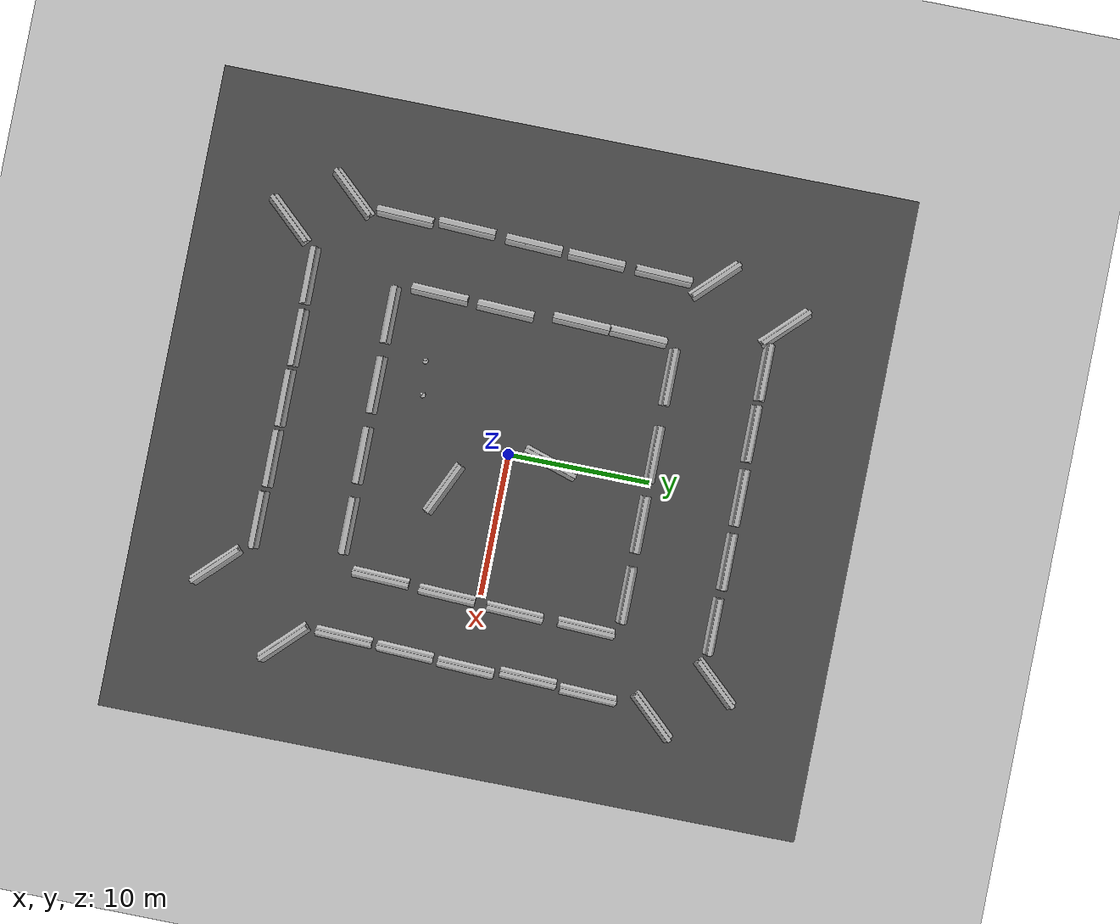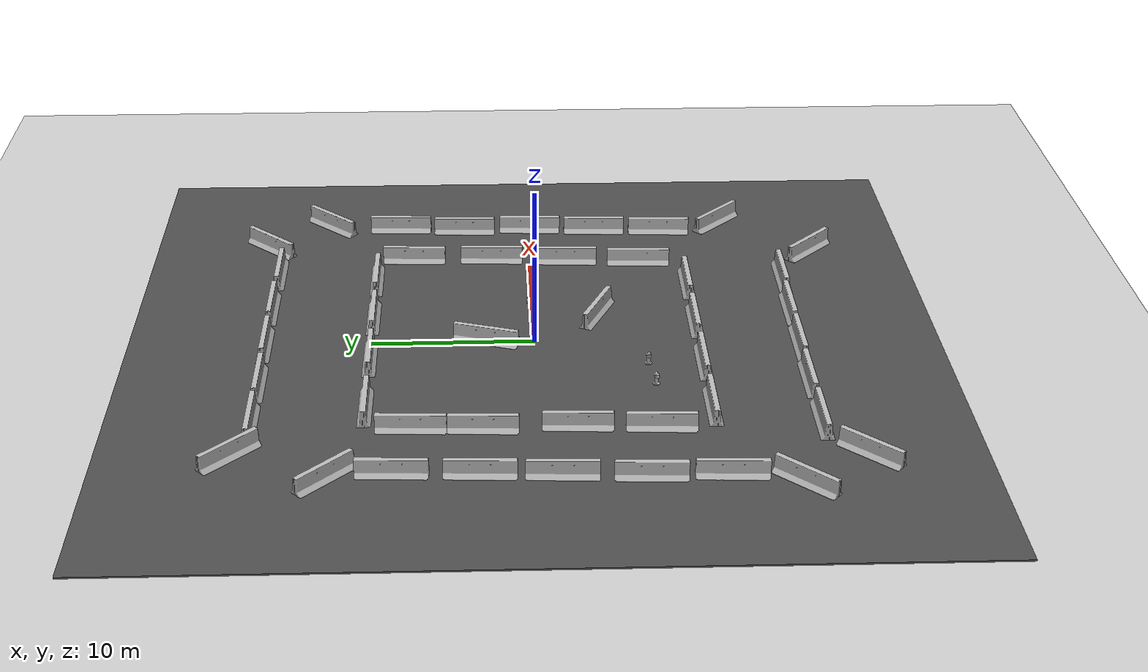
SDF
<sdf version="1.6">
 <world name="default">
  <light name="sun" type="directional">
   <pose>0 0 10 0 -0 0</pose>
   <diffuse>0.8 0.8 0.8 1</diffuse>
   <specular>0.2 0.2 0.2 1</specular>
   <attenuation>
    <range>1000</range>
    <constant>0.9</constant>
    <linear>0.01</linear>
    <quadratic>0.001</quadratic>
   </attenuation>
   <direction>-0.5 0.1 -0.9</direction>
  </light>
  <model name="ground_plane">
   <static>1</static>
   <link name="link">
    <collision name="collision">
     <geometry><plane><normal>0 0 1</normal><size>100 100</size></plane></geometry>
     <surface><friction><ode><mu>100</mu><mu2>50</mu2></ode></friction></surface>
    </collision>
    <visual name="visual">
     <cast_shadows>0</cast_shadows>
     <geometry><plane><normal>0 0 1</normal><size>100 100</size></plane></geometry>
     <material>
      <script><uri>file://media/materials/scripts/gazebo.material</uri><name>Gazebo/Grey</name></script>
     </material>
    </visual>
    <velocity_decay><linear>0</linear><angular>0</angular></velocity_decay>
   </link>
  </model>
  <physics name="default_physics" default="0" type="ode">
   <max_step_size>0.01</max_step_size>
   <real_time_factor>1</real_time_factor>
   <real_time_update_rate>100</real_time_update_rate>
  </physics>
  <scene><ambient>0.4 0.4 0.4 1</ambient><background>0.7 0.7 0.7 1</background><shadows>1</shadows></scene>
  <model name="jersey_barrier">
   <static>1</static>
   <link name="link">
    <visual name="visual">
     <geometry><mesh><uri>model://jersey_barrier/meshes/jersey_barrier.dae</uri></mesh></geometry>
    </visual>
    <collision name="upright">
     <pose>0 0 0.5715 0 -0 0</pose>
     <geometry><box><size>4.06542 0.3063 1.143</size></box></geometry>
    </collision>
    <collision name="base">
     <pose>0 0 0.032258 0 -0 0</pose>
     <geometry><box><size>4.06542 0.8107 0.064516</size></box></geometry>
    </collision>
    <collision name="base2">
     <pose>0 0 0.1 0 -0 0</pose>
     <geometry><box><size>4.06542 0.65 0.1</size></box></geometry>
    </collision>
    <collision name="base3">
     <pose>0 0 0.2 0 -0 0</pose>
     <geometry><box><size>4.06542 0.5 0.1</size></box></geometry>
    </collision>
    <collision name="left-angle">
     <pose>0 -0.224 0.2401 0.9 -0 0</pose>
     <geometry><box><size>4.06542 0.5 0.064516</size></box></geometry>
    </collision>
    <collision name="right-angle">
     <pose>0 0.224 0.2401 -0.9 0 0</pose>
     <geometry><box><size>4.06542 0.5 0.064516</size></box></geometry>
    </collision>
    <velocity_decay><linear>0</linear><angular>0</angular></velocity_decay>
   </link>
   <pose>-8 -10 0 0 -0 0</pose>
  </model>
  <model name="jersey_barrier_0">
   <static>1</static>
   <link name="link">
    <visual name="visual">
     <geometry><mesh><uri>model://jersey_barrier/meshes/jersey_barrier.dae</uri></mesh></geometry>
    </visual>
    <collision name="upright">
     <pose>0 0 0.5715 0 -0 0</pose>
     <geometry><box><size>4.06542 0.3063 1.143</size></box></geometry>
    </collision>
    <collision name="base">
     <pose>0 0 0.032258 0 -0 0</pose>
     <geometry><box><size>4.06542 0.8107 0.064516</size></box></geometry>
    </collision>
    <collision name="base2">
     <pose>0 0 0.1 0 -0 0</pose>
     <geometry><box><size>4.06542 0.65 0.1</size></box></geometry>
    </collision>
    <collision name="base3">
     <pose>0 0 0.2 0 -0 0</pose>
     <geometry><box><size>4.06542 0.5 0.1</size></box></geometry>
    </collision>
    <collision name="left-angle">
     <pose>0 -0.224 0.2401 0.9 -0 0</pose>
     <geometry><box><size>4.06542 0.5 0.064516</size></box></geometry>
    </collision>
    <collision name="right-angle">
     <pose>0 0.224 0.2401 -0.9 0 0</pose>
     <geometry><box><size>4.06542 0.5 0.064516</size></box></geometry>
    </collision>
    <velocity_decay><linear>0</linear><angular>0</angular></velocity_decay>
   </link>
   <pose>-3 -10 0 0 -0 0</pose>
  </model>
  <model name="jersey_barrier_1">
   <static>1</static>
   <link name="link">
    <visual name="visual">
     <geometry><mesh><uri>model://jersey_barrier/meshes/jersey_barrier.dae</uri></mesh></geometry>
    </visual>
    <collision name="upright">
     <pose>0 0 0.5715 0 -0 0</pose>
     <geometry><box><size>4.06542 0.3063 1.143</size></box></geometry>
    </collision>
    <collision name="base">
     <pose>0 0 0.032258 0 -0 0</pose>
     <geometry><box><size>4.06542 0.8107 0.064516</size></box></geometry>
    </collision>
    <collision name="base2">
     <pose>0 0 0.1 0 -0 0</pose>
     <geometry><box><size>4.06542 0.65 0.1</size></box></geometry>
    </collision>
    <collision name="base3">
     <pose>0 0 0.2 0 -0 0</pose>
     <geometry><box><size>4.06542 0.5 0.1</size></box></geometry>
    </collision>
    <collision name="left-angle">
     <pose>0 -0.224 0.2401 0.9 -0 0</pose>
     <geometry><box><size>4.06542 0.5 0.064516</size></box></geometry>
    </collision>
    <collision name="right-angle">
     <pose>0 0.224 0.2401 -0.9 0 0</pose>
     <geometry><box><size>4.06542 0.5 0.064516</size></box></geometry>
    </collision>
    <velocity_decay><linear>0</linear><angular>0</angular></velocity_decay>
   </link>
   <pose>2 -10 0 0 -0 0</pose>
  </model>
  <model name="jersey_barrier_2">
   <static>1</static>
   <link name="link">
    <visual name="visual">
     <geometry><mesh><uri>model://jersey_barrier/meshes/jersey_barrier.dae</uri></mesh></geometry>
    </visual>
    <collision name="upright">
     <pose>0 0 0.5715 0 -0 0</pose>
     <geometry><box><size>4.06542 0.3063 1.143</size></box></geometry>
    </collision>
    <collision name="base">
     <pose>0 0 0.032258 0 -0 0</pose>
     <geometry><box><size>4.06542 0.8107 0.064516</size></box></geometry>
    </collision>
    <collision name="base2">
     <pose>0 0 0.1 0 -0 0</pose>
     <geometry><box><size>4.06542 0.65 0.1</size></box></geometry>
    </collision>
    <collision name="base3">
     <pose>0 0 0.2 0 -0 0</pose>
     <geometry><box><size>4.06542 0.5 0.1</size></box></geometry>
    </collision>
    <collision name="left-angle">
     <pose>0 -0.224 0.2401 0.9 -0 0</pose>
     <geometry><box><size>4.06542 0.5 0.064516</size></box></geometry>
    </collision>
    <collision name="right-angle">
     <pose>0 0.224 0.2401 -0.9 0 0</pose>
     <geometry><box><size>4.06542 0.5 0.064516</size></box></geometry>
    </collision>
    <velocity_decay><linear>0</linear><angular>0</angular></velocity_decay>
   </link>
   <pose>7 -10 0 0 -0 0</pose>
  </model>
  <model name="jersey_barrier_3">
   <static>1</static>
   <link name="link">
    <visual name="visual">
     <geometry><mesh><uri>model://jersey_barrier/meshes/jersey_barrier.dae</uri></mesh></geometry>
    </visual>
    <collision name="upright">
     <pose>0 0 0.5715 0 -0 0</pose>
     <geometry><box><size>4.06542 0.3063 1.143</size></box></geometry>
    </collision>
    <collision name="base">
     <pose>0 0 0.032258 0 -0 0</pose>
     <geometry><box><size>4.06542 0.8107 0.064516</size></box></geometry>
    </collision>
    <collision name="base2">
     <pose>0 0 0.1 0 -0 0</pose>
     <geometry><box><size>4.06542 0.65 0.1</size></box></geometry>
    </collision>
    <collision name="base3">
     <pose>0 0 0.2 0 -0 0</pose>
     <geometry><box><size>4.06542 0.5 0.1</size></box></geometry>
    </collision>
    <collision name="left-angle">
     <pose>0 -0.224 0.2401 0.9 -0 0</pose>
     <geometry><box><size>4.06542 0.5 0.064516</size></box></geometry>
    </collision>
    <collision name="right-angle">
     <pose>0 0.224 0.2401 -0.9 0 0</pose>
     <geometry><box><size>4.06542 0.5 0.064516</size></box></geometry>
    </collision>
    <velocity_decay><linear>0</linear><angular>0</angular></velocity_decay>
   </link>
   <pose>-7.50675 10 0 0 -0 0</pose>
  </model>
  <model name="jersey_barrier_4">
   <static>1</static>
   <link name="link">
    <visual name="visual">
     <geometry><mesh><uri>model://jersey_barrier/meshes/jersey_barrier.dae</uri></mesh></geometry>
    </visual>
    <collision name="upright">
     <pose>0 0 0.5715 0 -0 0</pose>
     <geometry><box><size>4.06542 0.3063 1.143</size></box></geometry>
    </collision>
    <collision name="base">
     <pose>0 0 0.032258 0 -0 0</pose>
     <geometry><box><size>4.06542 0.8107 0.064516</size></box></geometry>
    </collision>
    <collision name="base2">
     <pose>0 0 0.1 0 -0 0</pose>
     <geometry><box><size>4.06542 0.65 0.1</size></box></geometry>
    </collision>
    <collision name="base3">
     <pose>0 0 0.2 0 -0 0</pose>
     <geometry><box><size>4.06542 0.5 0.1</size></box></geometry>
    </collision>
    <collision name="left-angle">
     <pose>0 -0.224 0.2401 0.9 -0 0</pose>
     <geometry><box><size>4.06542 0.5 0.064516</size></box></geometry>
    </collision>
    <collision name="right-angle">
     <pose>0 0.224 0.2401 -0.9 0 0</pose>
     <geometry><box><size>4.06542 0.5 0.064516</size></box></geometry>
    </collision>
    <velocity_decay><linear>0</linear><angular>0</angular></velocity_decay>
   </link>
   <pose>-2 10 0 0 -0 0</pose>
  </model>
  <model name="jersey_barrier_5">
   <static>1</static>
   <link name="link">
    <visual name="visual">
     <geometry><mesh><uri>model://jersey_barrier/meshes/jersey_barrier.dae</uri></mesh></geometry>
    </visual>
    <collision name="upright">
     <pose>0 0 0.5715 0 -0 0</pose>
     <geometry><box><size>4.06542 0.3063 1.143</size></box></geometry>
    </collision>
    <collision name="base">
     <pose>0 0 0.032258 0 -0 0</pose>
     <geometry><box><size>4.06542 0.8107 0.064516</size></box></geometry>
    </collision>
    <collision name="base2">
     <pose>0 0 0.1 0 -0 0</pose>
     <geometry><box><size>4.06542 0.65 0.1</size></box></geometry>
    </collision>
    <collision name="base3">
     <pose>0 0 0.2 0 -0 0</pose>
     <geometry><box><size>4.06542 0.5 0.1</size></box></geometry>
    </collision>
    <collision name="left-angle">
     <pose>0 -0.224 0.2401 0.9 -0 0</pose>
     <geometry><box><size>4.06542 0.5 0.064516</size></box></geometry>
    </collision>
    <collision name="right-angle">
     <pose>0 0.224 0.2401 -0.9 0 0</pose>
     <geometry><box><size>4.06542 0.5 0.064516</size></box></geometry>
    </collision>
    <velocity_decay><linear>0</linear><angular>0</angular></velocity_decay>
   </link>
   <pose>3 10 0 0 -0 0</pose>
  </model>
  <model name="jersey_barrier_6">
   <static>1</static>
   <link name="link">
    <visual name="visual">
     <geometry><mesh><uri>model://jersey_barrier/meshes/jersey_barrier.dae</uri></mesh></geometry>
    </visual>
    <collision name="upright">
     <pose>0 0 0.5715 0 -0 0</pose>
     <geometry><box><size>4.06542 0.3063 1.143</size></box></geometry>
    </collision>
    <collision name="base">
     <pose>0 0 0.032258 0 -0 0</pose>
     <geometry><box><size>4.06542 0.8107 0.064516</size></box></geometry>
    </collision>
    <collision name="base2">
     <pose>0 0 0.1 0 -0 0</pose>
     <geometry><box><size>4.06542 0.65 0.1</size></box></geometry>
    </collision>
    <collision name="base3">
     <pose>0 0 0.2 0 -0 0</pose>
     <geometry><box><size>4.06542 0.5 0.1</size></box></geometry>
    </collision>
    <collision name="left-angle">
     <pose>0 -0.224 0.2401 0.9 -0 0</pose>
     <geometry><box><size>4.06542 0.5 0.064516</size></box></geometry>
    </collision>
    <collision name="right-angle">
     <pose>0 0.224 0.2401 -0.9 0 0</pose>
     <geometry><box><size>4.06542 0.5 0.064516</size></box></geometry>
    </collision>
    <velocity_decay><linear>0</linear><angular>0</angular></velocity_decay>
   </link>
   <pose>8 10 0 0 -0 0</pose>
  </model>
  <model name="asphalt_plane">
   <static>1</static>
   <link name="link">
    <collision name="collision"><geometry><box><size>45.6368 49.6066 0.1</size></box></geometry></collision>
    <visual name="visual">
     <cast_shadows>0</cast_shadows>
     <geometry><box><size>45.6368 49.6066 0.1</size></box></geometry>
     <material>
      <script>
       <uri>model://asphalt_plane/materials/scripts</uri>
       <uri>model://asphalt_plane/materials/textures</uri>
       <name>vrc/asphalt</name>
      </script>
     </material>
    </visual>
    <velocity_decay><linear>0</linear><angular>0</angular></velocity_decay>
   </link>
   <pose>-0.123803 0.022176 0 0 -0 0</pose>
  </model>
  <gravity>0 0 -9.8</gravity>
  <magnetic_field>6e-06 2.3e-05 -4.2e-05</magnetic_field>
  <atmosphere type="adiabatic"/>
  <audio><device>default</device></audio>
  <spherical_coordinates>
   <surface_model>EARTH_WGS84</surface_model>
   <latitude_deg>0</latitude_deg>
   <longitude_deg>0</longitude_deg>
   <elevation>0</elevation>
   <heading_deg>0</heading_deg>
  </spherical_coordinates>
  <model name="jersey_barrier_7">
   <static>1</static>
   <link name="link">
    <visual name="visual">
     <geometry><mesh><uri>model://jersey_barrier/meshes/jersey_barrier.dae</uri></mesh></geometry>
    </visual>
    <collision name="upright">
     <pose>0 0 0.5715 0 -0 0</pose>
     <geometry><box><size>4.06542 0.3063 1.143</size></box></geometry>
    </collision>
    <collision name="base">
     <pose>0 0 0.032258 0 -0 0</pose>
     <geometry><box><size>4.06542 0.8107 0.064516</size></box></geometry>
    </collision>
    <collision name="base2">
     <pose>0 0 0.1 0 -0 0</pose>
     <geometry><box><size>4.06542 0.65 0.1</size></box></geometry>
    </collision>
    <collision name="base3">
     <pose>0 0 0.2 0 -0 0</pose>
     <geometry><box><size>4.06542 0.5 0.1</size></box></geometry>
    </collision>
    <collision name="left-angle">
     <pose>0 -0.224 0.2401 0.9 -0 0</pose>
     <geometry><box><size>4.06542 0.5 0.064516</size></box></geometry>
    </collision>
    <collision name="right-angle">
     <pose>0 0.224 0.2401 -0.9 0 0</pose>
     <geometry><box><size>4.06542 0.5 0.064516</size></box></geometry>
    </collision>
   </link>
   <pose>10.1442 -7.0827 0 0 -0 1.5316</pose>
  </model>
  <model name="jersey_barrier_7_clone">
   <static>1</static>
   <link name="link">
    <visual name="visual">
     <geometry><mesh><uri>model://jersey_barrier/meshes/jersey_barrier.dae</uri></mesh></geometry>
    </visual>
    <collision name="upright">
     <pose>0 0 0.5715 0 -0 0</pose>
     <geometry><box><size>4.06542 0.3063 1.143</size></box></geometry>
    </collision>
    <collision name="base">
     <pose>0 0 0.032258 0 -0 0</pose>
     <geometry><box><size>4.06542 0.8107 0.064516</size></box></geometry>
    </collision>
    <collision name="base2">
     <pose>0 0 0.1 0 -0 0</pose>
     <geometry><box><size>4.06542 0.65 0.1</size></box></geometry>
    </collision>
    <collision name="base3">
     <pose>0 0 0.2 0 -0 0</pose>
     <geometry><box><size>4.06542 0.5 0.1</size></box></geometry>
    </collision>
    <collision name="left-angle">
     <pose>0 -0.224 0.2401 0.9 -0 0</pose>
     <geometry><box><size>4.06542 0.5 0.064516</size></box></geometry>
    </collision>
    <collision name="right-angle">
     <pose>0 0.224 0.2401 -0.9 0 0</pose>
     <geometry><box><size>4.06542 0.5 0.064516</size></box></geometry>
    </collision>
   </link>
   <pose>10.4384 -2.30893 0 0 -0 1.5316</pose>
  </model>
  <model name="jersey_barrier_7_clone_0">
   <static>1</static>
   <link name="link">
    <visual name="visual">
     <geometry><mesh><uri>model://jersey_barrier/meshes/jersey_barrier.dae</uri></mesh></geometry>
    </visual>
    <collision name="upright">
     <pose>0 0 0.5715 0 -0 0</pose>
     <geometry><box><size>4.06542 0.3063 1.143</size></box></geometry>
    </collision>
    <collision name="base">
     <pose>0 0 0.032258 0 -0 0</pose>
     <geometry><box><size>4.06542 0.8107 0.064516</size></box></geometry>
    </collision>
    <collision name="base2">
     <pose>0 0 0.1 0 -0 0</pose>
     <geometry><box><size>4.06542 0.65 0.1</size></box></geometry>
    </collision>
    <collision name="base3">
     <pose>0 0 0.2 0 -0 0</pose>
     <geometry><box><size>4.06542 0.5 0.1</size></box></geometry>
    </collision>
    <collision name="left-angle">
     <pose>0 -0.224 0.2401 0.9 -0 0</pose>
     <geometry><box><size>4.06542 0.5 0.064516</size></box></geometry>
    </collision>
    <collision name="right-angle">
     <pose>0 0.224 0.2401 -0.9 0 0</pose>
     <geometry><box><size>4.06542 0.5 0.064516</size></box></geometry>
    </collision>
   </link>
   <pose>10.7124 2.55807 0 0 -0 1.5316</pose>
  </model>
  <model name="jersey_barrier_7_clone_1">
   <static>1</static>
   <link name="link">
    <visual name="visual">
     <geometry><mesh><uri>model://jersey_barrier/meshes/jersey_barrier.dae</uri></mesh></geometry>
    </visual>
    <collision name="upright">
     <pose>0 0 0.5715 0 -0 0</pose>
     <geometry><box><size>4.06542 0.3063 1.143</size></box></geometry>
    </collision>
    <collision name="base">
     <pose>0 0 0.032258 0 -0 0</pose>
     <geometry><box><size>4.06542 0.8107 0.064516</size></box></geometry>
    </collision>
    <collision name="base2">
     <pose>0 0 0.1 0 -0 0</pose>
     <geometry><box><size>4.06542 0.65 0.1</size></box></geometry>
    </collision>
    <collision name="base3">
     <pose>0 0 0.2 0 -0 0</pose>
     <geometry><box><size>4.06542 0.5 0.1</size></box></geometry>
    </collision>
    <collision name="left-angle">
     <pose>0 -0.224 0.2401 0.9 -0 0</pose>
     <geometry><box><size>4.06542 0.5 0.064516</size></box></geometry>
    </collision>
    <collision name="right-angle">
     <pose>0 0.224 0.2401 -0.9 0 0</pose>
     <geometry><box><size>4.06542 0.5 0.064516</size></box></geometry>
    </collision>
   </link>
   <pose>10.8167 7.65912 0 0 -0 1.5316</pose>
  </model>
  <model name="jersey_barrier_7_clone_1_clone">
   <static>1</static>
   <link name="link">
    <visual name="visual">
     <geometry><mesh><uri>model://jersey_barrier/meshes/jersey_barrier.dae</uri></mesh></geometry>
    </visual>
    <collision name="upright">
     <pose>0 0 0.5715 0 -0 0</pose>
     <geometry><box><size>4.06542 0.3063 1.143</size></box></geometry>
    </collision>
    <collision name="base">
     <pose>0 0 0.032258 0 -0 0</pose>
     <geometry><box><size>4.06542 0.8107 0.064516</size></box></geometry>
    </collision>
    <collision name="base2">
     <pose>0 0 0.1 0 -0 0</pose>
     <geometry><box><size>4.06542 0.65 0.1</size></box></geometry>
    </collision>
    <collision name="base3">
     <pose>0 0 0.2 0 -0 0</pose>
     <geometry><box><size>4.06542 0.5 0.1</size></box></geometry>
    </collision>
    <collision name="left-angle">
     <pose>0 -0.224 0.2401 0.9 -0 0</pose>
     <geometry><box><size>4.06542 0.5 0.064516</size></box></geometry>
    </collision>
    <collision name="right-angle">
     <pose>0 0.224 0.2401 -0.9 0 0</pose>
     <geometry><box><size>4.06542 0.5 0.064516</size></box></geometry>
    </collision>
   </link>
   <pose>-9.88681 7.31742 0 0 -0 1.5316</pose>
  </model>
  <model name="jersey_barrier_7_clone_1_clone_0">
   <static>1</static>
   <link name="link">
    <visual name="visual">
     <geometry><mesh><uri>model://jersey_barrier/meshes/jersey_barrier.dae</uri></mesh></geometry>
    </visual>
    <collision name="upright">
     <pose>0 0 0.5715 0 -0 0</pose>
     <geometry><box><size>4.06542 0.3063 1.143</size></box></geometry>
    </collision>
    <collision name="base">
     <pose>0 0 0.032258 0 -0 0</pose>
     <geometry><box><size>4.06542 0.8107 0.064516</size></box></geometry>
    </collision>
    <collision name="base2">
     <pose>0 0 0.1 0 -0 0</pose>
     <geometry><box><size>4.06542 0.65 0.1</size></box></geometry>
    </collision>
    <collision name="base3">
     <pose>0 0 0.2 0 -0 0</pose>
     <geometry><box><size>4.06542 0.5 0.1</size></box></geometry>
    </collision>
    <collision name="left-angle">
     <pose>0 -0.224 0.2401 0.9 -0 0</pose>
     <geometry><box><size>4.06542 0.5 0.064516</size></box></geometry>
    </collision>
    <collision name="right-angle">
     <pose>0 0.224 0.2401 -0.9 0 0</pose>
     <geometry><box><size>4.06542 0.5 0.064516</size></box></geometry>
    </collision>
   </link>
   <pose>-10.0917 -6.86582 0 0 -0 1.5316</pose>
  </model>
  <model name="jersey_barrier_7_clone_1_clone_1">
   <static>1</static>
   <link name="link">
    <visual name="visual">
     <geometry><mesh><uri>model://jersey_barrier/meshes/jersey_barrier.dae</uri></mesh></geometry>
    </visual>
    <collision name="upright">
     <pose>0 0 0.5715 0 -0 0</pose>
     <geometry><box><size>4.06542 0.3063 1.143</size></box></geometry>
    </collision>
    <collision name="base">
     <pose>0 0 0.032258 0 -0 0</pose>
     <geometry><box><size>4.06542 0.8107 0.064516</size></box></geometry>
    </collision>
    <collision name="base2">
     <pose>0 0 0.1 0 -0 0</pose>
     <geometry><box><size>4.06542 0.65 0.1</size></box></geometry>
    </collision>
    <collision name="base3">
     <pose>0 0 0.2 0 -0 0</pose>
     <geometry><box><size>4.06542 0.5 0.1</size></box></geometry>
    </collision>
    <collision name="left-angle">
     <pose>0 -0.224 0.2401 0.9 -0 0</pose>
     <geometry><box><size>4.06542 0.5 0.064516</size></box></geometry>
    </collision>
    <collision name="right-angle">
     <pose>0 0.224 0.2401 -0.9 0 0</pose>
     <geometry><box><size>4.06542 0.5 0.064516</size></box></geometry>
    </collision>
   </link>
   <pose>-14.3801 8.23059 0 0 -0 1.5316</pose>
  </model>
  <model name="jersey_barrier_7_clone_1_clone_2">
   <static>1</static>
   <link name="link">
    <visual name="visual">
     <geometry><mesh><uri>model://jersey_barrier/meshes/jersey_barrier.dae</uri></mesh></geometry>
    </visual>
    <collision name="upright">
     <pose>0 0 0.5715 0 -0 0</pose>
     <geometry><box><size>4.06542 0.3063 1.143</size></box></geometry>
    </collision>
    <collision name="base">
     <pose>0 0 0.032258 0 -0 0</pose>
     <geometry><box><size>4.06542 0.8107 0.064516</size></box></geometry>
    </collision>
    <collision name="base2">
     <pose>0 0 0.1 0 -0 0</pose>
     <geometry><box><size>4.06542 0.65 0.1</size></box></geometry>
    </collision>
    <collision name="base3">
     <pose>0 0 0.2 0 -0 0</pose>
     <geometry><box><size>4.06542 0.5 0.1</size></box></geometry>
    </collision>
    <collision name="left-angle">
     <pose>0 -0.224 0.2401 0.9 -0 0</pose>
     <geometry><box><size>4.06542 0.5 0.064516</size></box></geometry>
    </collision>
    <collision name="right-angle">
     <pose>0 0.224 0.2401 -0.9 0 0</pose>
     <geometry><box><size>4.06542 0.5 0.064516</size></box></geometry>
    </collision>
   </link>
   <pose>-14.5541 3.41634 0 0 -0 1.5316</pose>
  </model>
  <model name="jersey_barrier_7_clone_1_clone_3">
   <static>1</static>
   <link name="link">
    <visual name="visual">
     <geometry><mesh><uri>model://jersey_barrier/meshes/jersey_barrier.dae</uri></mesh></geometry>
    </visual>
    <collision name="upright">
     <pose>0 0 0.5715 0 -0 0</pose>
     <geometry><box><size>4.06542 0.3063 1.143</size></box></geometry>
    </collision>
    <collision name="base">
     <pose>0 0 0.032258 0 -0 0</pose>
     <geometry><box><size>4.06542 0.8107 0.064516</size></box></geometry>
    </collision>
    <collision name="base2">
     <pose>0 0 0.1 0 -0 0</pose>
     <geometry><box><size>4.06542 0.65 0.1</size></box></geometry>
    </collision>
    <collision name="base3">
     <pose>0 0 0.2 0 -0 0</pose>
     <geometry><box><size>4.06542 0.5 0.1</size></box></geometry>
    </collision>
    <collision name="left-angle">
     <pose>0 -0.224 0.2401 0.9 -0 0</pose>
     <geometry><box><size>4.06542 0.5 0.064516</size></box></geometry>
    </collision>
    <collision name="right-angle">
     <pose>0 0.224 0.2401 -0.9 0 0</pose>
     <geometry><box><size>4.06542 0.5 0.064516</size></box></geometry>
    </collision>
   </link>
   <pose>-14.7486 -1.06823 0 0 -0 1.5316</pose>
  </model>
  <model name="jersey_barrier_7_clone_1_clone_4">
   <static>1</static>
   <link name="link">
    <visual name="visual">
     <geometry><mesh><uri>model://jersey_barrier/meshes/jersey_barrier.dae</uri></mesh></geometry>
    </visual>
    <collision name="upright">
     <pose>0 0 0.5715 0 -0 0</pose>
     <geometry><box><size>4.06542 0.3063 1.143</size></box></geometry>
    </collision>
    <collision name="base">
     <pose>0 0 0.032258 0 -0 0</pose>
     <geometry><box><size>4.06542 0.8107 0.064516</size></box></geometry>
    </collision>
    <collision name="base2">
     <pose>0 0 0.1 0 -0 0</pose>
     <geometry><box><size>4.06542 0.65 0.1</size></box></geometry>
    </collision>
    <collision name="base3">
     <pose>0 0 0.2 0 -0 0</pose>
     <geometry><box><size>4.06542 0.5 0.1</size></box></geometry>
    </collision>
    <collision name="left-angle">
     <pose>0 -0.224 0.2401 0.9 -0 0</pose>
     <geometry><box><size>4.06542 0.5 0.064516</size></box></geometry>
    </collision>
    <collision name="right-angle">
     <pose>0 0.224 0.2401 -0.9 0 0</pose>
     <geometry><box><size>4.06542 0.5 0.064516</size></box></geometry>
    </collision>
   </link>
   <pose>-14.9922 -5.87235 0 0 -0 1.5316</pose>
  </model>
  <model name="jersey_barrier_7_clone_1_clone_5">
   <static>1</static>
   <link name="link">
    <visual name="visual">
     <geometry><mesh><uri>model://jersey_barrier/meshes/jersey_barrier.dae</uri></mesh></geometry>
    </visual>
    <collision name="upright">
     <pose>0 0 0.5715 0 -0 0</pose>
     <geometry><box><size>4.06542 0.3063 1.143</size></box></geometry>
    </collision>
    <collision name="base">
     <pose>0 0 0.032258 0 -0 0</pose>
     <geometry><box><size>4.06542 0.8107 0.064516</size></box></geometry>
    </collision>
    <collision name="base2">
     <pose>0 0 0.1 0 -0 0</pose>
     <geometry><box><size>4.06542 0.65 0.1</size></box></geometry>
    </collision>
    <collision name="base3">
     <pose>0 0 0.2 0 -0 0</pose>
     <geometry><box><size>4.06542 0.5 0.1</size></box></geometry>
    </collision>
    <collision name="left-angle">
     <pose>0 -0.224 0.2401 0.9 -0 0</pose>
     <geometry><box><size>4.06542 0.5 0.064516</size></box></geometry>
    </collision>
    <collision name="right-angle">
     <pose>0 0.224 0.2401 -0.9 0 0</pose>
     <geometry><box><size>4.06542 0.5 0.064516</size></box></geometry>
    </collision>
   </link>
   <pose>-14.959 -10.2795 0 0 -0 1.5316</pose>
  </model>
  <model name="jersey_barrier_6_clone">
   <static>1</static>
   <link name="link">
    <visual name="visual">
     <geometry><mesh><uri>model://jersey_barrier/meshes/jersey_barrier.dae</uri></mesh></geometry>
    </visual>
    <collision name="upright">
     <pose>0 0 0.5715 0 -0 0</pose>
     <geometry><box><size>4.06542 0.3063 1.143</size></box></geometry>
    </collision>
    <collision name="base">
     <pose>0 0 0.032258 0 -0 0</pose>
     <geometry><box><size>4.06542 0.8107 0.064516</size></box></geometry>
    </collision>
    <collision name="base2">
     <pose>0 0 0.1 0 -0 0</pose>
     <geometry><box><size>4.06542 0.65 0.1</size></box></geometry>
    </collision>
    <collision name="base3">
     <pose>0 0 0.2 0 -0 0</pose>
     <geometry><box><size>4.06542 0.5 0.1</size></box></geometry>
    </collision>
    <collision name="left-angle">
     <pose>0 -0.224 0.2401 0.9 -0 0</pose>
     <geometry><box><size>4.06542 0.5 0.064516</size></box></geometry>
    </collision>
    <collision name="right-angle">
     <pose>0 0.224 0.2401 -0.9 0 0</pose>
     <geometry><box><size>4.06542 0.5 0.064516</size></box></geometry>
    </collision>
    <velocity_decay><linear>0</linear><angular>0</angular></velocity_decay>
   </link>
   <pose>8.97438 16.3625 0 0 -0 0</pose>
  </model>
  <model name="jersey_barrier_6_clone_0">
   <static>1</static>
   <link name="link">
    <visual name="visual">
     <geometry><mesh><uri>model://jersey_barrier/meshes/jersey_barrier.dae</uri></mesh></geometry>
    </visual>
    <collision name="upright">
     <pose>0 0 0.5715 0 -0 0</pose>
     <geometry><box><size>4.06542 0.3063 1.143</size></box></geometry>
    </collision>
    <collision name="base">
     <pose>0 0 0.032258 0 -0 0</pose>
     <geometry><box><size>4.06542 0.8107 0.064516</size></box></geometry>
    </collision>
    <collision name="base2">
     <pose>0 0 0.1 0 -0 0</pose>
     <geometry><box><size>4.06542 0.65 0.1</size></box></geometry>
    </collision>
    <collision name="base3">
     <pose>0 0 0.2 0 -0 0</pose>
     <geometry><box><size>4.06542 0.5 0.1</size></box></geometry>
    </collision>
    <collision name="left-angle">
     <pose>0 -0.224 0.2401 0.9 -0 0</pose>
     <geometry><box><size>4.06542 0.5 0.064516</size></box></geometry>
    </collision>
    <collision name="right-angle">
     <pose>0 0.224 0.2401 -0.9 0 0</pose>
     <geometry><box><size>4.06542 0.5 0.064516</size></box></geometry>
    </collision>
    <velocity_decay><linear>0</linear><angular>0</angular></velocity_decay>
   </link>
   <pose>4.36549 16.4491 0 0 -0 0</pose>
  </model>
  <model name="jersey_barrier_6_clone_1">
   <static>1</static>
   <link name="link">
    <visual name="visual">
     <geometry><mesh><uri>model://jersey_barrier/meshes/jersey_barrier.dae</uri></mesh></geometry>
    </visual>
    <collision name="upright">
     <pose>0 0 0.5715 0 -0 0</pose>
     <geometry><box><size>4.06542 0.3063 1.143</size></box></geometry>
    </collision>
    <collision name="base">
     <pose>0 0 0.032258 0 -0 0</pose>
     <geometry><box><size>4.06542 0.8107 0.064516</size></box></geometry>
    </collision>
    <collision name="base2">
     <pose>0 0 0.1 0 -0 0</pose>
     <geometry><box><size>4.06542 0.65 0.1</size></box></geometry>
    </collision>
    <collision name="base3">
     <pose>0 0 0.2 0 -0 0</pose>
     <geometry><box><size>4.06542 0.5 0.1</size></box></geometry>
    </collision>
    <collision name="left-angle">
     <pose>0 -0.224 0.2401 0.9 -0 0</pose>
     <geometry><box><size>4.06542 0.5 0.064516</size></box></geometry>
    </collision>
    <collision name="right-angle">
     <pose>0 0.224 0.2401 -0.9 0 0</pose>
     <geometry><box><size>4.06542 0.5 0.064516</size></box></geometry>
    </collision>
    <velocity_decay><linear>0</linear><angular>0</angular></velocity_decay>
   </link>
   <pose>-0.186767 16.446 0 0 -0 0</pose>
  </model>
  <model name="jersey_barrier_6_clone_2">
   <static>1</static>
   <link name="link">
    <visual name="visual">
     <geometry><mesh><uri>model://jersey_barrier/meshes/jersey_barrier.dae</uri></mesh></geometry>
    </visual>
    <collision name="upright">
     <pose>0 0 0.5715 0 -0 0</pose>
     <geometry><box><size>4.06542 0.3063 1.143</size></box></geometry>
    </collision>
    <collision name="base">
     <pose>0 0 0.032258 0 -0 0</pose>
     <geometry><box><size>4.06542 0.8107 0.064516</size></box></geometry>
    </collision>
    <collision name="base2">
     <pose>0 0 0.1 0 -0 0</pose>
     <geometry><box><size>4.06542 0.65 0.1</size></box></geometry>
    </collision>
    <collision name="base3">
     <pose>0 0 0.2 0 -0 0</pose>
     <geometry><box><size>4.06542 0.5 0.1</size></box></geometry>
    </collision>
    <collision name="left-angle">
     <pose>0 -0.224 0.2401 0.9 -0 0</pose>
     <geometry><box><size>4.06542 0.5 0.064516</size></box></geometry>
    </collision>
    <collision name="right-angle">
     <pose>0 0.224 0.2401 -0.9 0 0</pose>
     <geometry><box><size>4.06542 0.5 0.064516</size></box></geometry>
    </collision>
    <velocity_decay><linear>0</linear><angular>0</angular></velocity_decay>
   </link>
   <pose>-4.72887 16.4044 0 0 -0 0</pose>
  </model>
  <model name="jersey_barrier_6_clone_3">
   <static>1</static>
   <link name="link">
    <visual name="visual">
     <geometry><mesh><uri>model://jersey_barrier/meshes/jersey_barrier.dae</uri></mesh></geometry>
    </visual>
    <collision name="upright">
     <pose>0 0 0.5715 0 -0 0</pose>
     <geometry><box><size>4.06542 0.3063 1.143</size></box></geometry>
    </collision>
    <collision name="base">
     <pose>0 0 0.032258 0 -0 0</pose>
     <geometry><box><size>4.06542 0.8107 0.064516</size></box></geometry>
    </collision>
    <collision name="base2">
     <pose>0 0 0.1 0 -0 0</pose>
     <geometry><box><size>4.06542 0.65 0.1</size></box></geometry>
    </collision>
    <collision name="base3">
     <pose>0 0 0.2 0 -0 0</pose>
     <geometry><box><size>4.06542 0.5 0.1</size></box></geometry>
    </collision>
    <collision name="left-angle">
     <pose>0 -0.224 0.2401 0.9 -0 0</pose>
     <geometry><box><size>4.06542 0.5 0.064516</size></box></geometry>
    </collision>
    <collision name="right-angle">
     <pose>0 0.224 0.2401 -0.9 0 0</pose>
     <geometry><box><size>4.06542 0.5 0.064516</size></box></geometry>
    </collision>
    <velocity_decay><linear>0</linear><angular>0</angular></velocity_decay>
   </link>
   <pose>-9.0937 16.4454 0 0 -0 0</pose>
  </model>
  <model name="jersey_barrier_7_clone_2">
   <static>1</static>
   <link name="link">
    <visual name="visual">
     <geometry><mesh><uri>model://jersey_barrier/meshes/jersey_barrier.dae</uri></mesh></geometry>
    </visual>
    <collision name="upright">
     <pose>0 0 0.5715 0 -0 0</pose>
     <geometry><box><size>4.06542 0.3063 1.143</size></box></geometry>
    </collision>
    <collision name="base">
     <pose>0 0 0.032258 0 -0 0</pose>
     <geometry><box><size>4.06542 0.8107 0.064516</size></box></geometry>
    </collision>
    <collision name="base2">
     <pose>0 0 0.1 0 -0 0</pose>
     <geometry><box><size>4.06542 0.65 0.1</size></box></geometry>
    </collision>
    <collision name="base3">
     <pose>0 0 0.2 0 -0 0</pose>
     <geometry><box><size>4.06542 0.5 0.1</size></box></geometry>
    </collision>
    <collision name="left-angle">
     <pose>0 -0.224 0.2401 0.9 -0 0</pose>
     <geometry><box><size>4.06542 0.5 0.064516</size></box></geometry>
    </collision>
    <collision name="right-angle">
     <pose>0 0.224 0.2401 -0.9 0 0</pose>
     <geometry><box><size>4.06542 0.5 0.064516</size></box></geometry>
    </collision>
   </link>
   <pose>14.6825 -8.81262 0 0 -0 1.5316</pose>
  </model>
  <model name="jersey_barrier_7_clone_3">
   <static>1</static>
   <link name="link">
    <visual name="visual">
     <geometry><mesh><uri>model://jersey_barrier/meshes/jersey_barrier.dae</uri></mesh></geometry>
    </visual>
    <collision name="upright">
     <pose>0 0 0.5715 0 -0 0</pose>
     <geometry><box><size>4.06542 0.3063 1.143</size></box></geometry>
    </collision>
    <collision name="base">
     <pose>0 0 0.032258 0 -0 0</pose>
     <geometry><box><size>4.06542 0.8107 0.064516</size></box></geometry>
    </collision>
    <collision name="base2">
     <pose>0 0 0.1 0 -0 0</pose>
     <geometry><box><size>4.06542 0.65 0.1</size></box></geometry>
    </collision>
    <collision name="base3">
     <pose>0 0 0.2 0 -0 0</pose>
     <geometry><box><size>4.06542 0.5 0.1</size></box></geometry>
    </collision>
    <collision name="left-angle">
     <pose>0 -0.224 0.2401 0.9 -0 0</pose>
     <geometry><box><size>4.06542 0.5 0.064516</size></box></geometry>
    </collision>
    <collision name="right-angle">
     <pose>0 0.224 0.2401 -0.9 0 0</pose>
     <geometry><box><size>4.06542 0.5 0.064516</size></box></geometry>
    </collision>
   </link>
   <pose>14.8943 -4.42382 0 0 -0 1.5316</pose>
  </model>
  <model name="jersey_barrier_7_clone_4">
   <static>1</static>
   <link name="link">
    <visual name="visual">
     <geometry><mesh><uri>model://jersey_barrier/meshes/jersey_barrier.dae</uri></mesh></geometry>
    </visual>
    <collision name="upright">
     <pose>0 0 0.5715 0 -0 0</pose>
     <geometry><box><size>4.06542 0.3063 1.143</size></box></geometry>
    </collision>
    <collision name="base">
     <pose>0 0 0.032258 0 -0 0</pose>
     <geometry><box><size>4.06542 0.8107 0.064516</size></box></geometry>
    </collision>
    <collision name="base2">
     <pose>0 0 0.1 0 -0 0</pose>
     <geometry><box><size>4.06542 0.65 0.1</size></box></geometry>
    </collision>
    <collision name="base3">
     <pose>0 0 0.2 0 -0 0</pose>
     <geometry><box><size>4.06542 0.5 0.1</size></box></geometry>
    </collision>
    <collision name="left-angle">
     <pose>0 -0.224 0.2401 0.9 -0 0</pose>
     <geometry><box><size>4.06542 0.5 0.064516</size></box></geometry>
    </collision>
    <collision name="right-angle">
     <pose>0 0.224 0.2401 -0.9 0 0</pose>
     <geometry><box><size>4.06542 0.5 0.064516</size></box></geometry>
    </collision>
   </link>
   <pose>15.1542 -0.062521 0 0 -0 1.5316</pose>
  </model>
  <model name="jersey_barrier_7_clone_5">
   <static>1</static>
   <link name="link">
    <visual name="visual">
     <geometry><mesh><uri>model://jersey_barrier/meshes/jersey_barrier.dae</uri></mesh></geometry>
    </visual>
    <collision name="upright">
     <pose>0 0 0.5715 0 -0 0</pose>
     <geometry><box><size>4.06542 0.3063 1.143</size></box></geometry>
    </collision>
    <collision name="base">
     <pose>0 0 0.032258 0 -0 0</pose>
     <geometry><box><size>4.06542 0.8107 0.064516</size></box></geometry>
    </collision>
    <collision name="base2">
     <pose>0 0 0.1 0 -0 0</pose>
     <geometry><box><size>4.06542 0.65 0.1</size></box></geometry>
    </collision>
    <collision name="base3">
     <pose>0 0 0.2 0 -0 0</pose>
     <geometry><box><size>4.06542 0.5 0.1</size></box></geometry>
    </collision>
    <collision name="left-angle">
     <pose>0 -0.224 0.2401 0.9 -0 0</pose>
     <geometry><box><size>4.06542 0.5 0.064516</size></box></geometry>
    </collision>
    <collision name="right-angle">
     <pose>0 0.224 0.2401 -0.9 0 0</pose>
     <geometry><box><size>4.06542 0.5 0.064516</size></box></geometry>
    </collision>
   </link>
   <pose>15.0397 4.35414 0 0 -0 1.5316</pose>
  </model>
  <model name="jersey_barrier_7_clone_6">
   <static>1</static>
   <link name="link">
    <visual name="visual">
     <geometry><mesh><uri>model://jersey_barrier/meshes/jersey_barrier.dae</uri></mesh></geometry>
    </visual>
    <collision name="upright">
     <pose>0 0 0.5715 0 -0 0</pose>
     <geometry><box><size>4.06542 0.3063 1.143</size></box></geometry>
    </collision>
    <collision name="base">
     <pose>0 0 0.032258 0 -0 0</pose>
     <geometry><box><size>4.06542 0.8107 0.064516</size></box></geometry>
    </collision>
    <collision name="base2">
     <pose>0 0 0.1 0 -0 0</pose>
     <geometry><box><size>4.06542 0.65 0.1</size></box></geometry>
    </collision>
    <collision name="base3">
     <pose>0 0 0.2 0 -0 0</pose>
     <geometry><box><size>4.06542 0.5 0.1</size></box></geometry>
    </collision>
    <collision name="left-angle">
     <pose>0 -0.224 0.2401 0.9 -0 0</pose>
     <geometry><box><size>4.06542 0.5 0.064516</size></box></geometry>
    </collision>
    <collision name="right-angle">
     <pose>0 0.224 0.2401 -0.9 0 0</pose>
     <geometry><box><size>4.06542 0.5 0.064516</size></box></geometry>
    </collision>
   </link>
   <pose>15.3673 8.67832 0 0 -0 1.5316</pose>
  </model>
  <model name="jersey_barrier_clone">
   <static>1</static>
   <link name="link">
    <visual name="visual">
     <geometry><mesh><uri>model://jersey_barrier/meshes/jersey_barrier.dae</uri></mesh></geometry>
    </visual>
    <collision name="upright">
     <pose>0 0 0.5715 0 -0 0</pose>
     <geometry><box><size>4.06542 0.3063 1.143</size></box></geometry>
    </collision>
    <collision name="base">
     <pose>0 0 0.032258 0 -0 0</pose>
     <geometry><box><size>4.06542 0.8107 0.064516</size></box></geometry>
    </collision>
    <collision name="base2">
     <pose>0 0 0.1 0 -0 0</pose>
     <geometry><box><size>4.06542 0.65 0.1</size></box></geometry>
    </collision>
    <collision name="base3">
     <pose>0 0 0.2 0 -0 0</pose>
     <geometry><box><size>4.06542 0.5 0.1</size></box></geometry>
    </collision>
    <collision name="left-angle">
     <pose>0 -0.224 0.2401 0.9 -0 0</pose>
     <geometry><box><size>4.06542 0.5 0.064516</size></box></geometry>
    </collision>
    <collision name="right-angle">
     <pose>0 0.224 0.2401 -0.9 0 0</pose>
     <geometry><box><size>4.06542 0.5 0.064516</size></box></geometry>
    </collision>
    <velocity_decay><linear>0</linear><angular>0</angular></velocity_decay>
   </link>
   <pose>-9.60671 -16.051 0 0 -0 0</pose>
  </model>
  <model name="jersey_barrier_clone_0">
   <static>1</static>
   <link name="link">
    <visual name="visual">
     <geometry><mesh><uri>model://jersey_barrier/meshes/jersey_barrier.dae</uri></mesh></geometry>
    </visual>
    <collision name="upright">
     <pose>0 0 0.5715 0 -0 0</pose>
     <geometry><box><size>4.06542 0.3063 1.143</size></box></geometry>
    </collision>
    <collision name="base">
     <pose>0 0 0.032258 0 -0 0</pose>
     <geometry><box><size>4.06542 0.8107 0.064516</size></box></geometry>
    </collision>
    <collision name="base2">
     <pose>0 0 0.1 0 -0 0</pose>
     <geometry><box><size>4.06542 0.65 0.1</size></box></geometry>
    </collision>
    <collision name="base3">
     <pose>0 0 0.2 0 -0 0</pose>
     <geometry><box><size>4.06542 0.5 0.1</size></box></geometry>
    </collision>
    <collision name="left-angle">
     <pose>0 -0.224 0.2401 0.9 -0 0</pose>
     <geometry><box><size>4.06542 0.5 0.064516</size></box></geometry>
    </collision>
    <collision name="right-angle">
     <pose>0 0.224 0.2401 -0.9 0 0</pose>
     <geometry><box><size>4.06542 0.5 0.064516</size></box></geometry>
    </collision>
    <velocity_decay><linear>0</linear><angular>0</angular></velocity_decay>
   </link>
   <pose>-5.17894 -16.0195 0 0 -0 0</pose>
  </model>
  <model name="jersey_barrier_clone_1">
   <static>1</static>
   <link name="link">
    <visual name="visual">
     <geometry><mesh><uri>model://jersey_barrier/meshes/jersey_barrier.dae</uri></mesh></geometry>
    </visual>
    <collision name="upright">
     <pose>0 0 0.5715 0 -0 0</pose>
     <geometry><box><size>4.06542 0.3063 1.143</size></box></geometry>
    </collision>
    <collision name="base">
     <pose>0 0 0.032258 0 -0 0</pose>
     <geometry><box><size>4.06542 0.8107 0.064516</size></box></geometry>
    </collision>
    <collision name="base2">
     <pose>0 0 0.1 0 -0 0</pose>
     <geometry><box><size>4.06542 0.65 0.1</size></box></geometry>
    </collision>
    <collision name="base3">
     <pose>0 0 0.2 0 -0 0</pose>
     <geometry><box><size>4.06542 0.5 0.1</size></box></geometry>
    </collision>
    <collision name="left-angle">
     <pose>0 -0.224 0.2401 0.9 -0 0</pose>
     <geometry><box><size>4.06542 0.5 0.064516</size></box></geometry>
    </collision>
    <collision name="right-angle">
     <pose>0 0.224 0.2401 -0.9 0 0</pose>
     <geometry><box><size>4.06542 0.5 0.064516</size></box></geometry>
    </collision>
    <velocity_decay><linear>0</linear><angular>0</angular></velocity_decay>
   </link>
   <pose>-0.872675 -16.1021 0 0 -0 0</pose>
  </model>
  <model name="jersey_barrier_clone_2">
   <static>1</static>
   <link name="link">
    <visual name="visual">
     <geometry><mesh><uri>model://jersey_barrier/meshes/jersey_barrier.dae</uri></mesh></geometry>
    </visual>
    <collision name="upright">
     <pose>0 0 0.5715 0 -0 0</pose>
     <geometry><box><size>4.06542 0.3063 1.143</size></box></geometry>
    </collision>
    <collision name="base">
     <pose>0 0 0.032258 0 -0 0</pose>
     <geometry><box><size>4.06542 0.8107 0.064516</size></box></geometry>
    </collision>
    <collision name="base2">
     <pose>0 0 0.1 0 -0 0</pose>
     <geometry><box><size>4.06542 0.65 0.1</size></box></geometry>
    </collision>
    <collision name="base3">
     <pose>0 0 0.2 0 -0 0</pose>
     <geometry><box><size>4.06542 0.5 0.1</size></box></geometry>
    </collision>
    <collision name="left-angle">
     <pose>0 -0.224 0.2401 0.9 -0 0</pose>
     <geometry><box><size>4.06542 0.5 0.064516</size></box></geometry>
    </collision>
    <collision name="right-angle">
     <pose>0 0.224 0.2401 -0.9 0 0</pose>
     <geometry><box><size>4.06542 0.5 0.064516</size></box></geometry>
    </collision>
    <velocity_decay><linear>0</linear><angular>0</angular></velocity_decay>
   </link>
   <pose>3.43298 -16.132 0 0 -0 0</pose>
  </model>
  <model name="jersey_barrier_clone_3">
   <static>1</static>
   <link name="link">
    <visual name="visual">
     <geometry><mesh><uri>model://jersey_barrier/meshes/jersey_barrier.dae</uri></mesh></geometry>
    </visual>
    <collision name="upright">
     <pose>0 0 0.5715 0 -0 0</pose>
     <geometry><box><size>4.06542 0.3063 1.143</size></box></geometry>
    </collision>
    <collision name="base">
     <pose>0 0 0.032258 0 -0 0</pose>
     <geometry><box><size>4.06542 0.8107 0.064516</size></box></geometry>
    </collision>
    <collision name="base2">
     <pose>0 0 0.1 0 -0 0</pose>
     <geometry><box><size>4.06542 0.65 0.1</size></box></geometry>
    </collision>
    <collision name="base3">
     <pose>0 0 0.2 0 -0 0</pose>
     <geometry><box><size>4.06542 0.5 0.1</size></box></geometry>
    </collision>
    <collision name="left-angle">
     <pose>0 -0.224 0.2401 0.9 -0 0</pose>
     <geometry><box><size>4.06542 0.5 0.064516</size></box></geometry>
    </collision>
    <collision name="right-angle">
     <pose>0 0.224 0.2401 -0.9 0 0</pose>
     <geometry><box><size>4.06542 0.5 0.064516</size></box></geometry>
    </collision>
    <velocity_decay><linear>0</linear><angular>0</angular></velocity_decay>
   </link>
   <pose>7.80452 -16.2737 0 0 -0 0</pose>
  </model>
  <model name="jersey_barrier_clone_4">
   <static>1</static>
   <link name="link">
    <visual name="visual">
     <geometry><mesh><uri>model://jersey_barrier/meshes/jersey_barrier.dae</uri></mesh></geometry>
    </visual>
    <collision name="upright">
     <pose>0 0 0.5715 0 -0 0</pose>
     <geometry><box><size>4.06542 0.3063 1.143</size></box></geometry>
    </collision>
    <collision name="base">
     <pose>0 0 0.032258 0 -0 0</pose>
     <geometry><box><size>4.06542 0.8107 0.064516</size></box></geometry>
    </collision>
    <collision name="base2">
     <pose>0 0 0.1 0 -0 0</pose>
     <geometry><box><size>4.06542 0.65 0.1</size></box></geometry>
    </collision>
    <collision name="base3">
     <pose>0 0 0.2 0 -0 0</pose>
     <geometry><box><size>4.06542 0.5 0.1</size></box></geometry>
    </collision>
    <collision name="left-angle">
     <pose>0 -0.224 0.2401 0.9 -0 0</pose>
     <geometry><box><size>4.06542 0.5 0.064516</size></box></geometry>
    </collision>
    <collision name="right-angle">
     <pose>0 0.224 0.2401 -0.9 0 0</pose>
     <geometry><box><size>4.06542 0.5 0.064516</size></box></geometry>
    </collision>
    <velocity_decay><linear>0</linear><angular>0</angular></velocity_decay>
   </link>
   <pose>11.4908 -18.5483 0 0 0 -0.792377</pose>
  </model>
  <model name="jersey_barrier_clone_4_clone">
   <static>1</static>
   <link name="link">
    <visual name="visual">
     <geometry><mesh><uri>model://jersey_barrier/meshes/jersey_barrier.dae</uri></mesh></geometry>
    </visual>
    <collision name="upright">
     <pose>0 0 0.5715 0 -0 0</pose>
     <geometry><box><size>4.06542 0.3063 1.143</size></box></geometry>
    </collision>
    <collision name="base">
     <pose>0 0 0.032258 0 -0 0</pose>
     <geometry><box><size>4.06542 0.8107 0.064516</size></box></geometry>
    </collision>
    <collision name="base2">
     <pose>0 0 0.1 0 -0 0</pose>
     <geometry><box><size>4.06542 0.65 0.1</size></box></geometry>
    </collision>
    <collision name="base3">
     <pose>0 0 0.2 0 -0 0</pose>
     <geometry><box><size>4.06542 0.5 0.1</size></box></geometry>
    </collision>
    <collision name="left-angle">
     <pose>0 -0.224 0.2401 0.9 -0 0</pose>
     <geometry><box><size>4.06542 0.5 0.064516</size></box></geometry>
    </collision>
    <collision name="right-angle">
     <pose>0 0.224 0.2401 -0.9 0 0</pose>
     <geometry><box><size>4.06542 0.5 0.064516</size></box></geometry>
    </collision>
    <velocity_decay><linear>0</linear><angular>0</angular></velocity_decay>
   </link>
   <pose>15.8712 -12.8663 0 0 0 -0.792377</pose>
  </model>
  <model name="jersey_barrier_clone_4_clone_0">
   <static>1</static>
   <link name="link">
    <visual name="visual">
     <geometry><mesh><uri>model://jersey_barrier/meshes/jersey_barrier.dae</uri></mesh></geometry>
    </visual>
    <collision name="upright">
     <pose>0 0 0.5715 0 -0 0</pose>
     <geometry><box><size>4.06542 0.3063 1.143</size></box></geometry>
    </collision>
    <collision name="base">
     <pose>0 0 0.032258 0 -0 0</pose>
     <geometry><box><size>4.06542 0.8107 0.064516</size></box></geometry>
    </collision>
    <collision name="base2">
     <pose>0 0 0.1 0 -0 0</pose>
     <geometry><box><size>4.06542 0.65 0.1</size></box></geometry>
    </collision>
    <collision name="base3">
     <pose>0 0 0.2 0 -0 0</pose>
     <geometry><box><size>4.06542 0.5 0.1</size></box></geometry>
    </collision>
    <collision name="left-angle">
     <pose>0 -0.224 0.2401 0.9 -0 0</pose>
     <geometry><box><size>4.06542 0.5 0.064516</size></box></geometry>
    </collision>
    <collision name="right-angle">
     <pose>0 0.224 0.2401 -0.9 0 0</pose>
     <geometry><box><size>4.06542 0.5 0.064516</size></box></geometry>
    </collision>
    <velocity_decay><linear>0</linear><angular>0</angular></velocity_decay>
   </link>
   <pose>-14.7266 11.8532 0 0 0 -0.792377</pose>
  </model>
  <model name="jersey_barrier_clone_4_clone_1">
   <static>1</static>
   <link name="link">
    <visual name="visual">
     <geometry><mesh><uri>model://jersey_barrier/meshes/jersey_barrier.dae</uri></mesh></geometry>
    </visual>
    <collision name="upright">
     <pose>0 0 0.5715 0 -0 0</pose>
     <geometry><box><size>4.06542 0.3063 1.143</size></box></geometry>
    </collision>
    <collision name="base">
     <pose>0 0 0.032258 0 -0 0</pose>
     <geometry><box><size>4.06542 0.8107 0.064516</size></box></geometry>
    </collision>
    <collision name="base2">
     <pose>0 0 0.1 0 -0 0</pose>
     <geometry><box><size>4.06542 0.65 0.1</size></box></geometry>
    </collision>
    <collision name="base3">
     <pose>0 0 0.2 0 -0 0</pose>
     <geometry><box><size>4.06542 0.5 0.1</size></box></geometry>
    </collision>
    <collision name="left-angle">
     <pose>0 -0.224 0.2401 0.9 -0 0</pose>
     <geometry><box><size>4.06542 0.5 0.064516</size></box></geometry>
    </collision>
    <collision name="right-angle">
     <pose>0 0.224 0.2401 -0.9 0 0</pose>
     <geometry><box><size>4.06542 0.5 0.064516</size></box></geometry>
    </collision>
    <velocity_decay><linear>0</linear><angular>0</angular></velocity_decay>
   </link>
   <pose>-12.4105 17.2728 0 0 0 -0.792377</pose>
  </model>
  <model name="jersey_barrier_clone_4_clone_2">
   <static>1</static>
   <link name="link">
    <visual name="visual">
     <geometry><mesh><uri>model://jersey_barrier/meshes/jersey_barrier.dae</uri></mesh></geometry>
    </visual>
    <collision name="upright">
     <pose>0 0 0.5715 0 -0 0</pose>
     <geometry><box><size>4.06542 0.3063 1.143</size></box></geometry>
    </collision>
    <collision name="base">
     <pose>0 0 0.032258 0 -0 0</pose>
     <geometry><box><size>4.06542 0.8107 0.064516</size></box></geometry>
    </collision>
    <collision name="base2">
     <pose>0 0 0.1 0 -0 0</pose>
     <geometry><box><size>4.06542 0.65 0.1</size></box></geometry>
    </collision>
    <collision name="base3">
     <pose>0 0 0.2 0 -0 0</pose>
     <geometry><box><size>4.06542 0.5 0.1</size></box></geometry>
    </collision>
    <collision name="left-angle">
     <pose>0 -0.224 0.2401 0.9 -0 0</pose>
     <geometry><box><size>4.06542 0.5 0.064516</size></box></geometry>
    </collision>
    <collision name="right-angle">
     <pose>0 0.224 0.2401 -0.9 0 0</pose>
     <geometry><box><size>4.06542 0.5 0.064516</size></box></geometry>
    </collision>
    <velocity_decay><linear>0</linear><angular>0</angular></velocity_decay>
   </link>
   <pose>-15.8045 -14.1655 0 0 -0 0.826051</pose>
  </model>
  <model name="jersey_barrier_clone_4_clone_2_clone">
   <static>1</static>
   <link name="link">
    <visual name="visual">
     <geometry><mesh><uri>model://jersey_barrier/meshes/jersey_barrier.dae</uri></mesh></geometry>
    </visual>
    <collision name="upright">
     <pose>0 0 0.5715 0 -0 0</pose>
     <geometry><box><size>4.06542 0.3063 1.143</size></box></geometry>
    </collision>
    <collision name="base">
     <pose>0 0 0.032258 0 -0 0</pose>
     <geometry><box><size>4.06542 0.8107 0.064516</size></box></geometry>
    </collision>
    <collision name="base2">
     <pose>0 0 0.1 0 -0 0</pose>
     <geometry><box><size>4.06542 0.65 0.1</size></box></geometry>
    </collision>
    <collision name="base3">
     <pose>0 0 0.2 0 -0 0</pose>
     <geometry><box><size>4.06542 0.5 0.1</size></box></geometry>
    </collision>
    <collision name="left-angle">
     <pose>0 -0.224 0.2401 0.9 -0 0</pose>
     <geometry><box><size>4.06542 0.5 0.064516</size></box></geometry>
    </collision>
    <collision name="right-angle">
     <pose>0 0.224 0.2401 -0.9 0 0</pose>
     <geometry><box><size>4.06542 0.5 0.064516</size></box></geometry>
    </collision>
    <velocity_decay><linear>0</linear><angular>0</angular></velocity_decay>
   </link>
   <pose>-13.1592 -18.1667 0 0 -0 0.826051</pose>
  </model>
  <model name="jersey_barrier_clone_4_clone_2_clone_0">
   <static>1</static>
   <link name="link">
    <visual name="visual">
     <geometry><mesh><uri>model://jersey_barrier/meshes/jersey_barrier.dae</uri></mesh></geometry>
    </visual>
    <collision name="upright">
     <pose>0 0 0.5715 0 -0 0</pose>
     <geometry><box><size>4.06542 0.3063 1.143</size></box></geometry>
    </collision>
    <collision name="base">
     <pose>0 0 0.032258 0 -0 0</pose>
     <geometry><box><size>4.06542 0.8107 0.064516</size></box></geometry>
    </collision>
    <collision name="base2">
     <pose>0 0 0.1 0 -0 0</pose>
     <geometry><box><size>4.06542 0.65 0.1</size></box></geometry>
    </collision>
    <collision name="base3">
     <pose>0 0 0.2 0 -0 0</pose>
     <geometry><box><size>4.06542 0.5 0.1</size></box></geometry>
    </collision>
    <collision name="left-angle">
     <pose>0 -0.224 0.2401 0.9 -0 0</pose>
     <geometry><box><size>4.06542 0.5 0.064516</size></box></geometry>
    </collision>
    <collision name="right-angle">
     <pose>0 0.224 0.2401 -0.9 0 0</pose>
     <geometry><box><size>4.06542 0.5 0.064516</size></box></geometry>
    </collision>
    <velocity_decay><linear>0</linear><angular>0</angular></velocity_decay>
   </link>
   <pose>12.8572 17.2331 0 0 -0 0.826051</pose>
  </model>
  <model name="jersey_barrier_clone_4_clone_2_clone_1">
   <static>1</static>
   <link name="link">
    <visual name="visual">
     <geometry><mesh><uri>model://jersey_barrier/meshes/jersey_barrier.dae</uri></mesh></geometry>
    </visual>
    <collision name="upright">
     <pose>0 0 0.5715 0 -0 0</pose>
     <geometry><box><size>4.06542 0.3063 1.143</size></box></geometry>
    </collision>
    <collision name="base">
     <pose>0 0 0.032258 0 -0 0</pose>
     <geometry><box><size>4.06542 0.8107 0.064516</size></box></geometry>
    </collision>
    <collision name="base2">
     <pose>0 0 0.1 0 -0 0</pose>
     <geometry><box><size>4.06542 0.65 0.1</size></box></geometry>
    </collision>
    <collision name="base3">
     <pose>0 0 0.2 0 -0 0</pose>
     <geometry><box><size>4.06542 0.5 0.1</size></box></geometry>
    </collision>
    <collision name="left-angle">
     <pose>0 -0.224 0.2401 0.9 -0 0</pose>
     <geometry><box><size>4.06542 0.5 0.064516</size></box></geometry>
    </collision>
    <collision name="right-angle">
     <pose>0 0.224 0.2401 -0.9 0 0</pose>
     <geometry><box><size>4.06542 0.5 0.064516</size></box></geometry>
    </collision>
    <velocity_decay><linear>0</linear><angular>0</angular></velocity_decay>
   </link>
   <pose>15.9769 13.3489 0 0 -0 0.826051</pose>
  </model>
  <model name="jersey_barrier_7_clone_1_clone_clone">
   <static>1</static>
   <link name="link">
    <visual name="visual">
     <geometry><mesh><uri>model://jersey_barrier/meshes/jersey_barrier.dae</uri></mesh></geometry>
    </visual>
    <collision name="upright">
     <pose>0 0 0.5715 0 -0 0</pose>
     <geometry><box><size>4.06542 0.3063 1.143</size></box></geometry>
    </collision>
    <collision name="base">
     <pose>0 0 0.032258 0 -0 0</pose>
     <geometry><box><size>4.06542 0.8107 0.064516</size></box></geometry>
    </collision>
    <collision name="base2">
     <pose>0 0 0.1 0 -0 0</pose>
     <geometry><box><size>4.06542 0.65 0.1</size></box></geometry>
    </collision>
    <collision name="base3">
     <pose>0 0 0.2 0 -0 0</pose>
     <geometry><box><size>4.06542 0.5 0.1</size></box></geometry>
    </collision>
    <collision name="left-angle">
     <pose>0 -0.224 0.2401 0.9 -0 0</pose>
     <geometry><box><size>4.06542 0.5 0.064516</size></box></geometry>
    </collision>
    <collision name="right-angle">
     <pose>0 0.224 0.2401 -0.9 0 0</pose>
     <geometry><box><size>4.06542 0.5 0.064516</size></box></geometry>
    </collision>
   </link>
   <pose>-10.0171 3.22202 0 0 -0 1.5316</pose>
  </model>
  <model name="jersey_barrier_7_clone_1_clone_clone_0">
   <static>1</static>
   <link name="link">
    <visual name="visual">
     <geometry><mesh><uri>model://jersey_barrier/meshes/jersey_barrier.dae</uri></mesh></geometry>
    </visual>
    <collision name="upright">
     <pose>0 0 0.5715 0 -0 0</pose>
     <geometry><box><size>4.06542 0.3063 1.143</size></box></geometry>
    </collision>
    <collision name="base">
     <pose>0 0 0.032258 0 -0 0</pose>
     <geometry><box><size>4.06542 0.8107 0.064516</size></box></geometry>
    </collision>
    <collision name="base2">
     <pose>0 0 0.1 0 -0 0</pose>
     <geometry><box><size>4.06542 0.65 0.1</size></box></geometry>
    </collision>
    <collision name="base3">
     <pose>0 0 0.2 0 -0 0</pose>
     <geometry><box><size>4.06542 0.5 0.1</size></box></geometry>
    </collision>
    <collision name="left-angle">
     <pose>0 -0.224 0.2401 0.9 -0 0</pose>
     <geometry><box><size>4.06542 0.5 0.064516</size></box></geometry>
    </collision>
    <collision name="right-angle">
     <pose>0 0.224 0.2401 -0.9 0 0</pose>
     <geometry><box><size>4.06542 0.5 0.064516</size></box></geometry>
    </collision>
   </link>
   <pose>-9.8719 -2.13548 0 0 -0 1.5316</pose>
  </model>
  <model name="husky_ur10">
   <model name="husky">
    <pose>0.073478 -0.007966 -0.116875 0 -0 0</pose>
    <link name="base_link">
     <collision name="collision">
      <pose>0 0 0.1 0 -0 0</pose>
      <geometry><box><size>1.0074 0.5709 0.2675</size></box></geometry>
     </collision>
     <inertial>
      <mass>33.855</mass>
      <pose>-0.085613 -0.00084 0.238145 0 -0 0</pose>
      <inertia>
       <ixx>2.2343</ixx>
       <ixy>-0.023642</ixy>
       <ixz>0.275174</ixz>
       <iyy>3.42518</iyy>
       <iyz>0.00239624</iyz>
       <izz>2.1241</izz>
      </inertia>
     </inertial>
     <visual name="base">
      <geometry><mesh><uri>model://husky/meshes/base_link.stl</uri></mesh></geometry>
      <material><script><name>Gazebo/FlatBlack</name><uri>__default__</uri></script></material>
     </visual>
     <visual name="top_plate">
      <geometry><mesh><uri>model://husky/meshes/top_plate.stl</uri></mesh></geometry>
      <material><script><name>Gazebo/Yellow</name><uri>__default__</uri></script></material>
     </visual>
     <visual name="front_bumper">
      <pose>0.47 0 0.091 0 -0 0</pose>
      <geometry><mesh><uri>model://husky/meshes/bumper.stl</uri></mesh></geometry>
      <material><script><name>Gazebo/FlatBlack</name><uri>__default__</uri></script></material>
     </visual>
     <visual name="rear_bumper">
      <pose>-0.47 0 0.091 0 -0 3.141</pose>
      <geometry><mesh><uri>model://husky/meshes/bumper.stl</uri></mesh></geometry>
      <material><script><name>Gazebo/FlatBlack</name><uri>__default__</uri></script></material>
     </visual>
     <visual name="user_rail">
      <pose>0.272 0 0.245 0 -0 0</pose>
      <geometry><mesh><uri>model://husky/meshes/user_rail.stl</uri></mesh></geometry>
      <material><script><name>Gazebo/Grey</name><uri>__default__</uri></script></material>
     </visual>
    </link>
    <link name="back_left_wheel">
     <pose>-0.256 0.285475 0.035 0 -0 0</pose>
     <inertial>
      <mass>2.6357</mass>
      <inertia>
       <ixx>0.0246688</ixx>
       <ixy>0</ixy>
       <ixz>0</ixz>
       <iyy>0.0246688</iyy>
       <iyz>0</iyz>
       <izz>0.0441058</izz>
      </inertia>
     </inertial>
     <collision name="back_left_wheel_collision">
      <pose>0 0 0 -1.5707 0 0</pose>
      <geometry><cylinder><radius>0.17775</radius><length>0.1143</length></cylinder></geometry>
      <surface>
       <friction><ode><mu>100000</mu><mu2>100000</mu2><slip1>0</slip1><slip2>0</slip2></ode></friction>
      </surface>
     </collision>
     <visual name="back_left_wheel">
      <pose>0 0 0 -3.14159 0 0</pose>
      <geometry><mesh><uri>model://husky/meshes/wheel.stl</uri></mesh></geometry>
      <material><script><name>Gazebo/Grey</name><uri>__default__</uri></script></material>
     </visual>
    </link>
    <joint name="back_left_joint" type="revolute">
     <parent>base_link</parent>
     <child>back_left_wheel</child>
     <axis>
      <xyz>0 1 0</xyz>
      <use_parent_model_frame>1</use_parent_model_frame>
      <limit><lower>-1e+16</lower><upper>1e+16</upper></limit>
      <dynamics><spring_reference>0</spring_reference><spring_stiffness>0</spring_stiffness></dynamics>
     </axis>
     <physics><ode><limit><cfm>0</cfm><erp>0.9</erp></limit></ode></physics>
    </joint>
    <link name="back_right_wheel">
     <pose>-0.256 -0.285475 0.035 0 -0 0</pose>
     <inertial>
      <mass>2.6357</mass>
      <inertia>
       <ixx>0.0246688</ixx>
       <ixy>0</ixy>
       <ixz>0</ixz>
       <iyy>0.0246688</iyy>
       <iyz>0</iyz>
       <izz>0.0441058</izz>
      </inertia>
     </inertial>
     <collision name="back_right_wheel_collision">
      <pose>0 0 0 -1.5707 0 0</pose>
      <geometry><cylinder><radius>0.17775</radius><length>0.1143</length></cylinder></geometry>
      <surface>
       <friction><ode><mu>100000</mu><mu2>100000</mu2><slip1>0</slip1><slip2>0</slip2></ode></friction>
      </surface>
     </collision>
     <visual name="back_right_wheel">
      <pose>0 0 0 -3.14159 0 0</pose>
      <geometry><mesh><uri>model://husky/meshes/wheel.stl</uri></mesh></geometry>
      <material><script><name>Gazebo/Grey</name><uri>__default__</uri></script></material>
     </visual>
    </link>
    <joint name="back_right_joint" type="revolute">
     <parent>base_link</parent>
     <child>back_right_wheel</child>
     <axis>
      <xyz>0 1 0</xyz>
      <use_parent_model_frame>1</use_parent_model_frame>
      <limit><lower>-1e+16</lower><upper>1e+16</upper></limit>
      <dynamics><spring_reference>0</spring_reference><spring_stiffness>0</spring_stiffness></dynamics>
     </axis>
     <physics><ode><limit><cfm>0</cfm><erp>0.9</erp></limit></ode></physics>
    </joint>
    <link name="front_left_wheel">
     <pose>0.256 0.285475 0.035 0 -0 0</pose>
     <inertial>
      <mass>2.6357</mass>
      <inertia>
       <ixx>0.0246688</ixx>
       <ixy>0</ixy>
       <ixz>0</ixz>
       <iyy>0.0246688</iyy>
       <iyz>0</iyz>
       <izz>0.0441058</izz>
      </inertia>
     </inertial>
     <collision name="front_left_wheel_collision">
      <pose>0 0 0 -1.5707 0 0</pose>
      <geometry><cylinder><radius>0.17775</radius><length>0.1143</length></cylinder></geometry>
      <surface>
       <friction><ode><mu>100000</mu><mu2>100000</mu2><slip1>0</slip1><slip2>0</slip2></ode></friction>
      </surface>
     </collision>
     <visual name="front_left_wheel">
      <pose>0 0 0 -3.14159 0 0</pose>
      <geometry><mesh><uri>model://husky/meshes/wheel.stl</uri></mesh></geometry>
      <material><script><name>Gazebo/Grey</name><uri>__default__</uri></script></material>
     </visual>
    </link>
    <joint name="front_left_joint" type="revolute">
     <parent>base_link</parent>
     <child>front_left_wheel</child>
     <axis>
      <xyz>0 1 0</xyz>
      <use_parent_model_frame>1</use_parent_model_frame>
      <limit><lower>-1e+16</lower><upper>1e+16</upper></limit>
      <dynamics><spring_reference>0</spring_reference><spring_stiffness>0</spring_stiffness></dynamics>
     </axis>
     <physics><ode><limit><cfm>0</cfm><erp>0.9</erp></limit></ode></physics>
    </joint>
    <link name="front_right_wheel">
     <pose>0.256 -0.285475 0.035 0 -0 0</pose>
     <inertial>
      <mass>2.6357</mass>
      <inertia>
       <ixx>0.0246688</ixx>
       <ixy>0</ixy>
       <ixz>0</ixz>
       <iyy>0.0246688</iyy>
       <iyz>0</iyz>
       <izz>0.0441058</izz>
      </inertia>
     </inertial>
     <collision name="front_right_wheel_collision">
      <pose>0 0 0 -1.5707 0 0</pose>
      <geometry><cylinder><radius>0.17775</radius><length>0.1143</length></cylinder></geometry>
      <surface>
       <friction><ode><mu>100000</mu><mu2>100000</mu2><slip1>0</slip1><slip2>0</slip2></ode></friction>
      </surface>
     </collision>
     <visual name="front_right_wheel">
      <pose>0 0 0 -3.14159 0 0</pose>
      <geometry><mesh><uri>model://husky/meshes/wheel.stl</uri></mesh></geometry>
      <material><script><name>Gazebo/Grey</name><uri>__default__</uri></script></material>
     </visual>
    </link>
    <joint name="front_right_joint" type="revolute">
     <parent>base_link</parent>
     <child>front_right_wheel</child>
     <axis>
      <xyz>0 1 0</xyz>
      <use_parent_model_frame>1</use_parent_model_frame>
      <limit><lower>-1e+16</lower><upper>1e+16</upper></limit>
      <dynamics><spring_reference>0</spring_reference><spring_stiffness>0</spring_stiffness></dynamics>
     </axis>
     <physics><ode><limit><cfm>0</cfm><erp>0.9</erp></limit></ode></physics>
    </joint>
    <plugin name="husky_diff_controller" filename="libhusky_gazebo_plugins.so">
     <alwaysOn>1</alwaysOn>
     <updateRate>100.0</updateRate>
     <backLeftJoint>back_left_joint</backLeftJoint>
     <backRightJoint>back_right_joint</backRightJoint>
     <frontLeftJoint>front_left_joint</frontLeftJoint>
     <frontRightJoint>front_right_joint</frontRightJoint>
     <wheelSeparation>0.5709</wheelSeparation>
     <wheelDiameter>0.3555</wheelDiameter>
     <torque>35</torque>
    </plugin>
   </model>
   <model name="ur10">
    <link name="base">
     <inertial>
      <mass>4</mass>
      <inertia>
       <ixx>0.00610633</ixx>
       <ixy>0</ixy>
       <ixz>0</ixz>
       <iyy>0.00610633</iyy>
       <iyz>0</iyz>
       <izz>0.01125</izz>
      </inertia>
     </inertial>
     <collision name="collision">
      <pose>0 0 0.019 0 -0 0</pose>
      <geometry><cylinder><radius>0.075</radius><length>0.038</length></cylinder></geometry>
     </collision>
     <visual name="visual"><geometry><mesh><uri>model://ur10/meshes/base.dae</uri></mesh></geometry></visual>
    </link>
    <link name="shoulder">
     <pose>0 0 0.1273 0 -0 0</pose>
     <inertial>
      <mass>7.778</mass>
      <inertia>
       <ixx>0.0314743</ixx>
       <ixy>0</ixy>
       <ixz>0</ixz>
       <iyy>0.0314743</iyy>
       <iyz>0</iyz>
       <izz>0.0218756</izz>
      </inertia>
     </inertial>
     <collision name="collision">
      <geometry><cylinder><radius>0.075</radius><length>0.177</length></cylinder></geometry>
     </collision>
     <visual name="visual"><geometry><mesh><uri>model://ur10/meshes/shoulder.dae</uri></mesh></geometry></visual>
    </link>
    <link name="upper_arm">
     <pose>0 0.220941 0.1273 3.14159 1.57079 3.14159</pose>
     <inertial>
      <pose>0 0 0.306 0 -0 0</pose>
      <mass>12.93</mass>
      <inertia>
       <ixx>0.421754</ixx>
       <ixy>0</ixy>
       <ixz>0</ixz>
       <iyy>0.421754</iyy>
       <iyz>0</iyz>
       <izz>0.0363656</izz>
      </inertia>
     </inertial>
     <collision name="collision1">
      <pose>0 -0.045 0 1.5707 -0 0</pose>
      <geometry><cylinder><radius>0.075</radius><length>0.177</length></cylinder></geometry>
     </collision>
     <collision name="collision2">
      <pose>0 -0.0436 0.32 0 -0 1.5707</pose>
      <geometry><cylinder><radius>0.058</radius><length>0.461</length></cylinder></geometry>
     </collision>
     <collision name="collision3">
      <pose>0 -0.04 0.613 1.5707 -0 0</pose>
      <geometry><cylinder><radius>0.058</radius><length>0.129</length></cylinder></geometry>
     </collision>
     <visual name="visual"><geometry><mesh><uri>model://ur10/meshes/upperarm.dae</uri></mesh></geometry></visual>
    </link>
    <link name="forearm">
     <pose>0.612 0.049041 0.1273 3.14159 1.57079 3.14159</pose>
     <inertial>
      <pose>0 0 0.28615 0 -0 0</pose>
      <mass>3.87</mass>
      <inertia>
       <ixx>0.11107</ixx>
       <ixy>0</ixy>
       <ixz>0</ixz>
       <iyy>0.11107</iyy>
       <iyz>0</iyz>
       <izz>0.0108844</izz>
      </inertia>
     </inertial>
     <collision name="collision1">
      <pose>0 0 0.001 1.5707 -0 0</pose>
      <geometry><cylinder><radius>0.058</radius><length>0.136</length></cylinder></geometry>
     </collision>
     <collision name="collision2">
      <pose>0 0 0.305 0 -0 1.5707</pose>
      <geometry><cylinder><radius>0.045</radius><length>0.447</length></cylinder></geometry>
     </collision>
     <collision name="collision3">
      <pose>0 0.001 0.5735 1.5707 -0 0</pose>
      <geometry><cylinder><radius>0.045</radius><length>0.119</length></cylinder></geometry>
     </collision>
     <visual name="visua"><geometry><mesh><uri>model://ur10/meshes/forearm.dae</uri></mesh></geometry></visual>
    </link>
    <link name="wrist_1">
     <pose>1.1843 0.049041 0.1273 3.14159 -0 3.14159</pose>
     <inertial>
      <mass>1.96</mass>
      <inertia>
       <ixx>0.00510825</ixx>
       <ixy>0</ixy>
       <ixz>0</ixz>
       <iyy>0.00510825</iyy>
       <iyz>0</iyz>
       <izz>0.0055125</izz>
      </inertia>
     </inertial>
     <collision name="collision">
      <pose>0 0.115 0.0025 0 -0 0</pose>
      <geometry><cylinder><radius>0.0455</radius><length>0.119</length></cylinder></geometry>
     </collision>
     <visual name="visual"><geometry><mesh><uri>model://ur10/meshes/wrist1.dae</uri></mesh></geometry></visual>
    </link>
    <link name="wrist_2">
     <pose>1.1843 0.163941 0.1273 3.14159 -0 3.14159</pose>
     <inertial>
      <mass>1.96</mass>
      <inertia>
       <ixx>0.00510825</ixx>
       <ixy>0</ixy>
       <ixz>0</ixz>
       <iyy>0.00510825</iyy>
       <iyz>0</iyz>
       <izz>0.0055125</izz>
      </inertia>
     </inertial>
     <collision name="collision">
      <pose>0 0.002 0.11659 1.5707 -0 0</pose>
      <geometry><cylinder><radius>0.0455</radius><length>0.119</length></cylinder></geometry>
     </collision>
     <visual name="visual"><geometry><mesh><uri>model://ur10/meshes/wrist2.dae</uri></mesh></geometry></visual>
    </link>
    <link name="wrist_3">
     <pose>1.1843 0.163941 0.0116 3.14159 -0 3.14159</pose>
     <inertial>
      <mass>0.202</mass>
      <inertia>
       <ixx>0.000526462</ixx>
       <ixy>0</ixy>
       <ixz>0</ixz>
       <iyy>0.000526462</iyy>
       <iyz>0</iyz>
       <izz>0.000568125</izz>
      </inertia>
     </inertial>
     <collision name="collision">
      <pose>0 0.0765 0 1.5707 -0 0</pose>
      <geometry><cylinder><radius>0.045</radius><length>0.031</length></cylinder></geometry>
     </collision>
     <visual name="visual"><geometry><mesh><uri>model://ur10/meshes/wrist3.dae</uri></mesh></geometry></visual>
    </link>
    <joint name="shoulder_pan" type="revolute">
     <child>shoulder</child>
     <parent>base</parent>
     <axis>
      <xyz>0 0 1</xyz>
      <limit><lower>-6.28319</lower><upper>6.28319</upper><effort>330</effort><velocity>2.16</velocity></limit>
      <use_parent_model_frame>1</use_parent_model_frame>
      <dynamics><spring_reference>0</spring_reference><spring_stiffness>0</spring_stiffness></dynamics>
     </axis>
    </joint>
    <joint name="shoulder_lift" type="revolute">
     <child>upper_arm</child>
     <parent>shoulder</parent>
     <axis>
      <xyz>0 1 0</xyz>
      <limit><lower>-6.28319</lower><upper>6.28319</upper><effort>330</effort><velocity>2.16</velocity></limit>
      <use_parent_model_frame>1</use_parent_model_frame>
      <dynamics><spring_reference>0</spring_reference><spring_stiffness>0</spring_stiffness></dynamics>
     </axis>
    </joint>
    <joint name="elbow" type="revolute">
     <child>forearm</child>
     <parent>upper_arm</parent>
     <axis>
      <xyz>0 1 0</xyz>
      <limit><lower>-6.28319</lower><upper>6.28319</upper><effort>150</effort><velocity>3.15</velocity></limit>
      <use_parent_model_frame>1</use_parent_model_frame>
      <dynamics><spring_reference>0</spring_reference><spring_stiffness>0</spring_stiffness></dynamics>
     </axis>
    </joint>
    <joint name="wrist_1" type="revolute">
     <child>wrist_1</child>
     <parent>forearm</parent>
     <axis>
      <xyz>0 1 0</xyz>
      <limit><lower>-6.28319</lower><upper>6.28319</upper><effort>54</effort><velocity>3.2</velocity></limit>
      <use_parent_model_frame>1</use_parent_model_frame>
      <dynamics><spring_reference>0</spring_reference><spring_stiffness>0</spring_stiffness></dynamics>
     </axis>
    </joint>
    <joint name="wrist_2" type="revolute">
     <child>wrist_2</child>
     <parent>wrist_1</parent>
     <axis>
      <xyz>0 0 -1</xyz>
      <limit><lower>-6.28319</lower><upper>6.28319</upper><effort>54</effort><velocity>3.2</velocity></limit>
      <use_parent_model_frame>1</use_parent_model_frame>
      <dynamics><spring_reference>0</spring_reference><spring_stiffness>0</spring_stiffness></dynamics>
     </axis>
    </joint>
    <joint name="wrist_3" type="revolute">
     <child>wrist_3</child>
     <parent>wrist_2</parent>
     <axis>
      <xyz>0 1 0</xyz>
      <limit><lower>-6.28319</lower><upper>6.28319</upper><effort>54</effort><velocity>3.2</velocity></limit>
      <use_parent_model_frame>1</use_parent_model_frame>
      <dynamics><spring_reference>0</spring_reference><spring_stiffness>0</spring_stiffness></dynamics>
     </axis>
    </joint>
    <pose>-0.073478 0.007961 0.116875 0 -0 0</pose>
   </model>
   <joint name="base_link_JOINT_0" type="revolute">
    <parent>husky::base_link</parent>
    <child>ur10::base</child>
    <axis>
     <xyz>0 0 1</xyz>
     <use_parent_model_frame>0</use_parent_model_frame>
     <limit>
      <lower>-1.79769e+308</lower>
      <upper>1.79769e+308</upper>
      <effort>-1</effort>
      <velocity>-1</velocity>
     </limit>
     <dynamics>
      <spring_reference>0</spring_reference>
      <spring_stiffness>0</spring_stiffness>
      <damping>0</damping>
     </dynamics>
    </axis>
    <physics>
     <ode><limit><cfm>0</cfm><erp>0.2</erp></limit><suspension><cfm>0</cfm><erp>0.2</erp></suspension></ode>
    </physics>
   </joint>
   <static>0</static>
   <pose>5.19385 0.050917 0.30972 -2e-05 0.000128 3.11936</pose>
  </model>
  <model name="fire_hydrant">
   <static>1</static>
   <link name="link">
    <collision name="collision">
     <geometry><mesh><uri>model://fire_hydrant/meshes/fire_hydrant.dae</uri></mesh></geometry>
    </collision>
    <visual name="visual">
     <geometry><mesh><uri>model://fire_hydrant/meshes/fire_hydrant.dae</uri></mesh></geometry>
    </visual>
   </link>
   <pose>-5.31556 -6.96439 0 0 -0 0</pose>
  </model>
  <model name="fire_hydrant_0">
   <static>1</static>
   <link name="link">
    <collision name="collision">
     <geometry><mesh><uri>model://fire_hydrant/meshes/fire_hydrant.dae</uri></mesh></geometry>
    </collision>
    <visual name="visual">
     <geometry><mesh><uri>model://fire_hydrant/meshes/fire_hydrant.dae</uri></mesh></geometry>
    </visual>
   </link>
   <pose>-2.95066 -6.69342 0 0 -0 0</pose>
  </model>
  <model name="jersey_barrier_8">
   <static>1</static>
   <link name="link">
    <visual name="visual">
     <geometry><mesh><uri>model://jersey_barrier/meshes/jersey_barrier.dae</uri></mesh></geometry>
    </visual>
    <collision name="upright">
     <pose>0 0 0.5715 0 -0 0</pose>
     <geometry><box><size>4.06542 0.3063 1.143</size></box></geometry>
    </collision>
    <collision name="base">
     <pose>0 0 0.032258 0 -0 0</pose>
     <geometry><box><size>4.06542 0.8107 0.064516</size></box></geometry>
    </collision>
    <collision name="base2">
     <pose>0 0 0.1 0 -0 0</pose>
     <geometry><box><size>4.06542 0.65 0.1</size></box></geometry>
    </collision>
    <collision name="base3">
     <pose>0 0 0.2 0 -0 0</pose>
     <geometry><box><size>4.06542 0.5 0.1</size></box></geometry>
    </collision>
    <collision name="left-angle">
     <pose>0 -0.224 0.2401 0.9 -0 0</pose>
     <geometry><box><size>4.06542 0.5 0.064516</size></box></geometry>
    </collision>
    <collision name="right-angle">
     <pose>0 0.224 0.2401 -0.9 0 0</pose>
     <geometry><box><size>4.06542 0.5 0.064516</size></box></geometry>
    </collision>
   </link>
   <pose>3.18929 -3.96818 0 0 -0 2.7062</pose>
  </model>
  <model name="jersey_barrier_8_clone">
   <static>1</static>
   <link name="link">
    <visual name="visual">
     <geometry><mesh><uri>model://jersey_barrier/meshes/jersey_barrier.dae</uri></mesh></geometry>
    </visual>
    <collision name="upright">
     <pose>0 0 0.5715 0 -0 0</pose>
     <geometry><box><size>4.06542 0.3063 1.143</size></box></geometry>
    </collision>
    <collision name="base">
     <pose>0 0 0.032258 0 -0 0</pose>
     <geometry><box><size>4.06542 0.8107 0.064516</size></box></geometry>
    </collision>
    <collision name="base2">
     <pose>0 0 0.1 0 -0 0</pose>
     <geometry><box><size>4.06542 0.65 0.1</size></box></geometry>
    </collision>
    <collision name="base3">
     <pose>0 0 0.2 0 -0 0</pose>
     <geometry><box><size>4.06542 0.5 0.1</size></box></geometry>
    </collision>
    <collision name="left-angle">
     <pose>0 -0.224 0.2401 0.9 -0 0</pose>
     <geometry><box><size>4.06542 0.5 0.064516</size></box></geometry>
    </collision>
    <collision name="right-angle">
     <pose>0 0.224 0.2401 -0.9 0 0</pose>
     <geometry><box><size>4.06542 0.5 0.064516</size></box></geometry>
    </collision>
   </link>
   <pose>-0.008512 2.98581 0 0 -0 -1.87722</pose>
  </model>
 </world>
</sdf>
